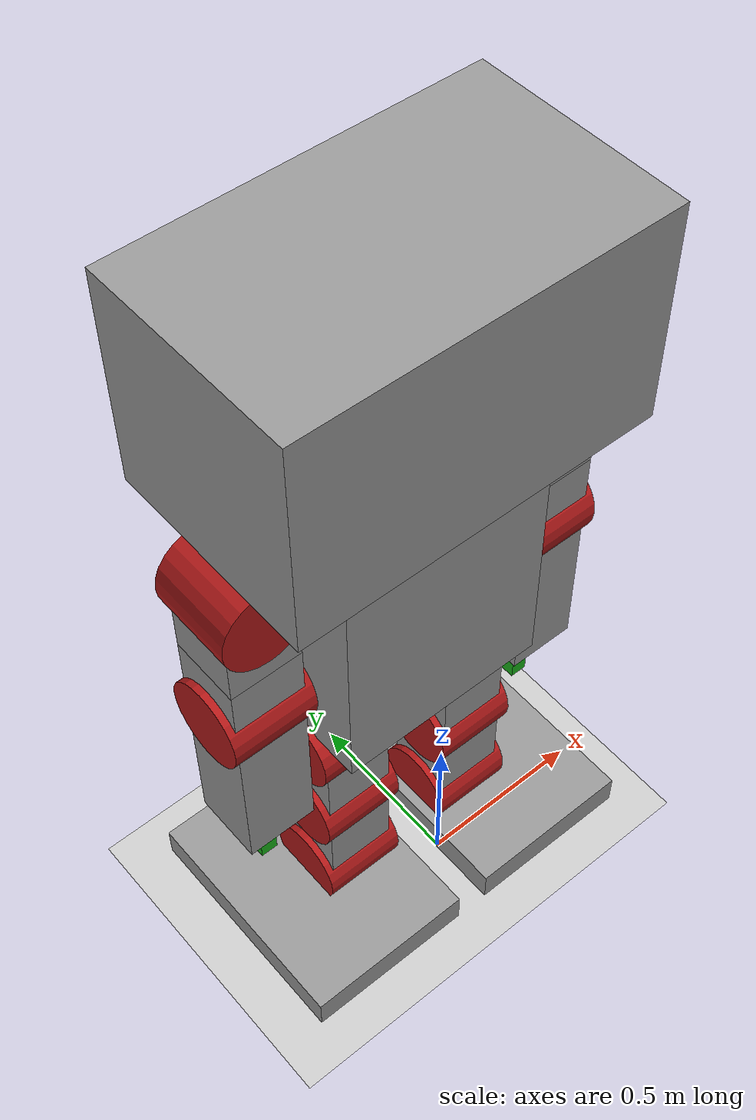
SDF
<sdf version="1.5">
 <world name="default">
  <light name="sun" type="directional">
   <pose>0 0 10 0.6 -0 0</pose>
   <diffuse>0.8 0.8 0.8 1</diffuse>
   <specular>0.2 0.2 0.2 1</specular>
   <attenuation>
    <range>1000</range>
    <constant>0.9</constant>
    <linear>0.01</linear>
    <quadratic>0.001</quadratic>
   </attenuation>
   <direction>-0.5 0.1 -0.9</direction>
  </light>
  <model name="ground_plane">
   <static>1</static>
   <link name="link">
    <collision name="collision">
     <geometry><plane><normal>0 0 1</normal><size>100 100</size></plane></geometry>
     <surface><friction><ode><mu>100</mu><mu2>50</mu2></ode></friction></surface>
    </collision>
    <visual name="visual">
     <cast_shadows>0</cast_shadows>
     <geometry><plane><normal>0 0 1</normal><size>100 100</size></plane></geometry>
     <material>
      <script><uri>file://media/materials/scripts/gazebo.material</uri><name>Gazebo/Grey</name></script>
     </material>
    </visual>
   </link>
  </model>
  <physics name="default_physics" default="0" type="ode">
   <max_step_size>0.001</max_step_size>
   <real_time_factor>1</real_time_factor>
   <real_time_update_rate>1000</real_time_update_rate>
   <gravity>0 0 -9.8</gravity>
   <magnetic_field>6e-06 2.3e-05 -4.2e-05</magnetic_field>
   <roki>
    <contact_info>
     <compensation>100</compensation>
     <relaxation>0.001</relaxation>
     <static_friction>3.0</static_friction>
     <friction>3.0</friction>
    </contact_info>
    <solver_type>Vert</solver_type>
    <debug_print>false</debug_print>
   </roki>
  </physics>
  <scene><ambient>0.4 0.4 0.4 1</ambient><background>0.7 0.7 0.7 1</background><shadows>1</shadows></scene>
  <audio><device>default</device></audio>
  <spherical_coordinates>
   <surface_model>EARTH_WGS84</surface_model>
   <latitude_deg>0</latitude_deg>
   <longitude_deg>0</longitude_deg>
   <elevation>0</elevation>
   <heading_deg>0</heading_deg>
  </spherical_coordinates>
  <model name="robo02">
   <plugin name="osc_pid_controller" filename="libosc_pid_controller_plugin.so">
    <osc_port>7000</osc_port>
    <joint name="hip_r_pitch" p="160" i="160" d="140" initial_value="0"/>
    <joint name="knee_r_pitch" p="160" i="160" d="140" initial_value="0"/>
    <joint name="heel_r_pitch" p="160" i="160" d="140" initial_value="0"/>
    <joint name="hip_l_pitch" p="160" i="160" d="140" initial_value="0"/>
    <joint name="knee_l_pitch" p="160" i="160" d="140" initial_value="0"/>
    <joint name="heel_l_pitch" p="160" i="160" d="140" initial_value="0"/>
    <joint name="shoulder_r_pitch" p="20" i="10" d="10" initial_value="0"/>
    <joint name="shoulder_r_roll" p="20" i="10" d="10" initial_value="0"/>
    <joint name="shoulder_r_yaw" p="20" i="10" d="10" initial_value="0"/>
    <joint name="elbow_r_pitch" p="20" i="10" d="10" initial_value="0"/>
    <joint name="shoulder_l_pitch" p="20" i="10" d="10" initial_value="0"/>
    <joint name="shoulder_l_roll" p="20" i="10" d="10" initial_value="0"/>
    <joint name="shoulder_l_yaw" p="20" i="10" d="10" initial_value="0"/>
    <joint name="elbow_l_pitch" p="20" i="10" d="10" initial_value="0"/>
    <capture_file>/home/test/capture.csv</capture_file>
   </plugin>
   <link name="link_0">
    <pose>-0.266944 -0.109722 1.83351 0 -0 0</pose>
    <inertial>
     <mass>1</mass>
     <inertia><ixx>1</ixx><ixy>0</ixy><ixz>0</ixz><iyy>1</iyy><iyz>0</iyz><izz>1</izz></inertia>
    </inertial>
    <visual name="visual">
     <geometry><box><size>0.6 0.4 0.8</size></box></geometry>
     <material>
      <lighting>1</lighting>
      <script><uri>file://media/materials/scripts/gazebo.material</uri><name>Gazebo/Grey</name></script>
      <shader type="pixel"><normal_map>__default__</normal_map></shader>
      <ambient>0.3 0.3 0.3 1</ambient>
      <diffuse>0.7 0.7 0.7 1</diffuse>
      <specular>0.01 0.01 0.01 1</specular>
      <emissive>0 0 0 1</emissive>
     </material>
    </visual>
    <collision name="collision">
     <geometry><box><size>0.6 0.4 0.8</size></box></geometry>
     <surface>
      <friction><ode><mu>1</mu><mu2>1</mu2><fdir1>0 0 0</fdir1><slip1>0</slip1><slip2>0</slip2></ode></friction>
      <bounce><restitution_coefficient>0</restitution_coefficient><threshold>1e+06</threshold></bounce>
      <contact>
       <collide_without_contact>0</collide_without_contact>
       <collide_without_contact_bitmask>1</collide_without_contact_bitmask>
       <collide_bitmask>1</collide_bitmask>
       <ode>
        <soft_cfm>0</soft_cfm>
        <soft_erp>0.2</soft_erp>
        <kp>1e+13</kp>
        <kd>1</kd>
        <max_vel>0.01</max_vel>
        <min_depth>0</min_depth>
       </ode>
       <bullet>
        <split_impulse>1</split_impulse>
        <split_impulse_penetration_threshold>-0.01</split_impulse_penetration_threshold>
        <soft_cfm>0</soft_cfm>
        <soft_erp>0.2</soft_erp>
        <kp>1e+13</kp>
        <kd>1</kd>
       </bullet>
      </contact>
     </surface>
    </collision>
   </link>
   <link name="link_1">
    <pose>-0.266944 -0.109722 2.53351 0 -0 0</pose>
    <inertial>
     <mass>0.1</mass>
     <inertia><ixx>1</ixx><ixy>0</ixy><ixz>0</ixz><iyy>1</iyy><iyz>0</iyz><izz>1</izz></inertia>
    </inertial>
    <visual name="visual">
     <geometry><box><size>1 0.6 0.6</size></box></geometry>
     <material>
      <lighting>1</lighting>
      <script><uri>file://media/materials/scripts/gazebo.material</uri><name>Gazebo/Grey</name></script>
      <shader type="pixel"><normal_map>__default__</normal_map></shader>
      <ambient>0.3 0.3 0.3 1</ambient>
      <diffuse>0.7 0.7 0.7 1</diffuse>
      <specular>0.01 0.01 0.01 1</specular>
      <emissive>0 0 0 1</emissive>
     </material>
    </visual>
    <collision name="collision">
     <geometry><box><size>1 0.6 0.6</size></box></geometry>
     <surface>
      <friction><ode><mu>1</mu><mu2>1</mu2><fdir1>0 0 0</fdir1><slip1>0</slip1><slip2>0</slip2></ode></friction>
      <bounce><restitution_coefficient>0</restitution_coefficient><threshold>1e+06</threshold></bounce>
      <contact>
       <collide_without_contact>0</collide_without_contact>
       <collide_without_contact_bitmask>1</collide_without_contact_bitmask>
       <collide_bitmask>1</collide_bitmask>
       <ode>
        <soft_cfm>0</soft_cfm>
        <soft_erp>0.2</soft_erp>
        <kp>1e+13</kp>
        <kd>1</kd>
        <max_vel>0.01</max_vel>
        <min_depth>0</min_depth>
       </ode>
       <bullet>
        <split_impulse>1</split_impulse>
        <split_impulse_penetration_threshold>-0.01</split_impulse_penetration_threshold>
        <soft_cfm>0</soft_cfm>
        <soft_erp>0.2</soft_erp>
        <kp>1e+13</kp>
        <kd>1</kd>
       </bullet>
      </contact>
     </surface>
    </collision>
   </link>
   <link name="link_11">
    <pose>0.183056 -0.109722 1.98351 0 -0 0</pose>
    <inertial>
     <mass>2</mass>
     <inertia><ixx>1</ixx><ixy>0</ixy><ixz>0</ixz><iyy>1</iyy><iyz>0</iyz><izz>1</izz></inertia>
    </inertial>
    <visual name="visual">
     <geometry><box><size>0.2 0.2 0.2</size></box></geometry>
     <material>
      <lighting>1</lighting>
      <script><uri>file://media/materials/scripts/gazebo.material</uri><name>Gazebo/Grey</name></script>
      <shader type="pixel"><normal_map>__default__</normal_map></shader>
      <ambient>0.3 0.3 0.3 1</ambient>
      <diffuse>0.7 0.7 0.7 1</diffuse>
      <specular>0.01 0.01 0.01 1</specular>
      <emissive>0 0 0 1</emissive>
     </material>
    </visual>
    <collision name="collision">
     <geometry><box><size>0.2 0.2 0.2</size></box></geometry>
     <surface>
      <friction><ode><mu>1</mu><mu2>1</mu2><fdir1>0 0 0</fdir1><slip1>0</slip1><slip2>0</slip2></ode></friction>
      <bounce><restitution_coefficient>0</restitution_coefficient><threshold>1e+06</threshold></bounce>
      <contact>
       <collide_without_contact>0</collide_without_contact>
       <collide_without_contact_bitmask>1</collide_without_contact_bitmask>
       <collide_bitmask>1</collide_bitmask>
       <ode>
        <soft_cfm>0</soft_cfm>
        <soft_erp>0.2</soft_erp>
        <kp>1e+13</kp>
        <kd>1</kd>
        <max_vel>0.01</max_vel>
        <min_depth>0</min_depth>
       </ode>
       <bullet>
        <split_impulse>1</split_impulse>
        <split_impulse_penetration_threshold>-0.01</split_impulse_penetration_threshold>
        <soft_cfm>0</soft_cfm>
        <soft_erp>0.2</soft_erp>
        <kp>1e+13</kp>
        <kd>1</kd>
       </bullet>
      </contact>
     </surface>
    </collision>
   </link>
   <link name="link_12">
    <pose>0.183056 -0.109722 1.78351 0 -0 0</pose>
    <inertial>
     <mass>0.2</mass>
     <inertia><ixx>1</ixx><ixy>0</ixy><ixz>0</ixz><iyy>1</iyy><iyz>0</iyz><izz>1</izz></inertia>
    </inertial>
    <visual name="visual">
     <geometry><box><size>0.2 0.2 0.2</size></box></geometry>
     <material>
      <lighting>1</lighting>
      <script><uri>file://media/materials/scripts/gazebo.material</uri><name>Gazebo/Grey</name></script>
      <shader type="pixel"><normal_map>__default__</normal_map></shader>
      <ambient>0.3 0.3 0.3 1</ambient>
      <diffuse>0.7 0.7 0.7 1</diffuse>
      <specular>0.01 0.01 0.01 1</specular>
      <emissive>0 0 0 1</emissive>
     </material>
    </visual>
    <collision name="collision">
     <geometry><box><size>0.2 0.2 0.2</size></box></geometry>
     <surface>
      <friction><ode><mu>1</mu><mu2>1</mu2><fdir1>0 0 0</fdir1><slip1>0</slip1><slip2>0</slip2></ode></friction>
      <bounce><restitution_coefficient>0</restitution_coefficient><threshold>1e+06</threshold></bounce>
      <contact>
       <collide_without_contact>0</collide_without_contact>
       <collide_without_contact_bitmask>1</collide_without_contact_bitmask>
       <collide_bitmask>1</collide_bitmask>
       <ode>
        <soft_cfm>0</soft_cfm>
        <soft_erp>0.2</soft_erp>
        <kp>1e+13</kp>
        <kd>1</kd>
        <max_vel>0.01</max_vel>
        <min_depth>0</min_depth>
       </ode>
       <bullet>
        <split_impulse>1</split_impulse>
        <split_impulse_penetration_threshold>-0.01</split_impulse_penetration_threshold>
        <soft_cfm>0</soft_cfm>
        <soft_erp>0.2</soft_erp>
        <kp>1e+13</kp>
        <kd>1</kd>
       </bullet>
      </contact>
     </surface>
    </collision>
   </link>
   <link name="link_13">
    <pose>0.183056 -0.109722 1.68351 3.14159 1.57079 3.14159</pose>
    <inertial>
     <mass>0.1</mass>
     <inertia><ixx>1</ixx><ixy>0</ixy><ixz>0</ixz><iyy>1</iyy><iyz>0</iyz><izz>1</izz></inertia>
    </inertial>
    <visual name="visual">
     <geometry><cylinder><radius>0.12</radius><length>0.24</length></cylinder></geometry>
     <material>
      <lighting>1</lighting>
      <script><uri>file://media/materials/scripts/gazebo.material</uri><name>Gazebo/Grey</name></script>
      <shader type="pixel"><normal_map>__default__</normal_map></shader>
      <ambient>0.3 0.3 0.3 1</ambient>
      <diffuse>0.7 0.1 0.1 1</diffuse>
      <specular>0.01 0.01 0.01 1</specular>
      <emissive>0 0 0 1</emissive>
     </material>
    </visual>
    <collision name="collision">
     <geometry><cylinder><radius>0.12</radius><length>0.24</length></cylinder></geometry>
     <surface>
      <friction><ode><mu>1</mu><mu2>1</mu2><fdir1>0 0 0</fdir1><slip1>0</slip1><slip2>0</slip2></ode></friction>
      <bounce><restitution_coefficient>0</restitution_coefficient><threshold>1e+06</threshold></bounce>
      <contact>
       <collide_without_contact>0</collide_without_contact>
       <collide_without_contact_bitmask>1</collide_without_contact_bitmask>
       <collide_bitmask>1</collide_bitmask>
       <ode>
        <soft_cfm>0</soft_cfm>
        <soft_erp>0.2</soft_erp>
        <kp>1e+13</kp>
        <kd>1</kd>
        <max_vel>0.01</max_vel>
        <min_depth>0</min_depth>
       </ode>
       <bullet>
        <split_impulse>1</split_impulse>
        <split_impulse_penetration_threshold>-0.01</split_impulse_penetration_threshold>
        <soft_cfm>0</soft_cfm>
        <soft_erp>0.2</soft_erp>
        <kp>1e+13</kp>
        <kd>1</kd>
       </bullet>
      </contact>
     </surface>
    </collision>
   </link>
   <link name="link_14">
    <pose>0.183056 -0.109722 1.43351 0 -0 0</pose>
    <inertial>
     <mass>0.2</mass>
     <inertia><ixx>1</ixx><ixy>0</ixy><ixz>0</ixz><iyy>1</iyy><iyz>0</iyz><izz>1</izz></inertia>
    </inertial>
    <visual name="visual">
     <geometry><box><size>0.2 0.2 0.5</size></box></geometry>
     <material>
      <lighting>1</lighting>
      <script><uri>file://media/materials/scripts/gazebo.material</uri><name>Gazebo/Grey</name></script>
      <shader type="pixel"><normal_map>__default__</normal_map></shader>
      <ambient>0.3 0.3 0.3 1</ambient>
      <diffuse>0.7 0.7 0.7 1</diffuse>
      <specular>0.01 0.01 0.01 1</specular>
      <emissive>0 0 0 1</emissive>
     </material>
    </visual>
    <collision name="collision">
     <geometry><box><size>0.2 0.2 0.5</size></box></geometry>
     <surface>
      <friction><ode><mu>1</mu><mu2>1</mu2><fdir1>0 0 0</fdir1><slip1>0</slip1><slip2>0</slip2></ode></friction>
      <bounce><restitution_coefficient>0</restitution_coefficient><threshold>1e+06</threshold></bounce>
      <contact>
       <collide_without_contact>0</collide_without_contact>
       <collide_without_contact_bitmask>1</collide_without_contact_bitmask>
       <collide_bitmask>1</collide_bitmask>
       <ode>
        <soft_cfm>0</soft_cfm>
        <soft_erp>0.2</soft_erp>
        <kp>1e+13</kp>
        <kd>1</kd>
        <max_vel>0.01</max_vel>
        <min_depth>0</min_depth>
       </ode>
       <bullet>
        <split_impulse>1</split_impulse>
        <split_impulse_penetration_threshold>-0.01</split_impulse_penetration_threshold>
        <soft_cfm>0</soft_cfm>
        <soft_erp>0.2</soft_erp>
        <kp>1e+13</kp>
        <kd>1</kd>
       </bullet>
      </contact>
     </surface>
    </collision>
   </link>
   <link name="link_15">
    <pose>-0.466944 -0.109722 1.33351 3.14159 1.57079 3.14159</pose>
    <inertial>
     <mass>0.1</mass>
     <inertia><ixx>1</ixx><ixy>0</ixy><ixz>0</ixz><iyy>1</iyy><iyz>0</iyz><izz>1</izz></inertia>
    </inertial>
    <visual name="visual">
     <geometry><cylinder><radius>0.12</radius><length>0.24</length></cylinder></geometry>
     <material>
      <lighting>1</lighting>
      <script><uri>file://media/materials/scripts/gazebo.material</uri><name>Gazebo/Grey</name></script>
      <shader type="pixel"><normal_map>__default__</normal_map></shader>
      <ambient>0.3 0.3 0.3 1</ambient>
      <diffuse>0.7 0.1 0.1 1</diffuse>
      <specular>0.01 0.01 0.01 1</specular>
      <emissive>0 0 0 1</emissive>
     </material>
    </visual>
    <collision name="collision">
     <geometry><cylinder><radius>0.12</radius><length>0.24</length></cylinder></geometry>
     <surface>
      <friction><ode><mu>1</mu><mu2>1</mu2><fdir1>0 0 0</fdir1><slip1>0</slip1><slip2>0</slip2></ode></friction>
      <bounce><restitution_coefficient>0</restitution_coefficient><threshold>1e+06</threshold></bounce>
      <contact>
       <collide_without_contact>0</collide_without_contact>
       <collide_without_contact_bitmask>1</collide_without_contact_bitmask>
       <collide_bitmask>1</collide_bitmask>
       <ode>
        <soft_cfm>0</soft_cfm>
        <soft_erp>0.2</soft_erp>
        <kp>1e+13</kp>
        <kd>1</kd>
        <max_vel>0.01</max_vel>
        <min_depth>0</min_depth>
       </ode>
       <bullet>
        <split_impulse>1</split_impulse>
        <split_impulse_penetration_threshold>-0.01</split_impulse_penetration_threshold>
        <soft_cfm>0</soft_cfm>
        <soft_erp>0.2</soft_erp>
        <kp>1e+13</kp>
        <kd>1</kd>
       </bullet>
      </contact>
     </surface>
    </collision>
   </link>
   <link name="link_16">
    <pose>-0.466944 -0.109722 1.18351 0 -0 0</pose>
    <inertial>
     <mass>0.2</mass>
     <inertia><ixx>1</ixx><ixy>0</ixy><ixz>0</ixz><iyy>1</iyy><iyz>0</iyz><izz>1</izz></inertia>
    </inertial>
    <visual name="visual">
     <geometry><box><size>0.2 0.2 0.3</size></box></geometry>
     <material>
      <lighting>1</lighting>
      <script><uri>file://media/materials/scripts/gazebo.material</uri><name>Gazebo/Grey</name></script>
      <shader type="pixel"><normal_map>__default__</normal_map></shader>
      <ambient>0.3 0.3 0.3 1</ambient>
      <diffuse>0.7 0.7 0.7 1</diffuse>
      <specular>0.01 0.01 0.01 1</specular>
      <emissive>0 0 0 1</emissive>
     </material>
    </visual>
    <collision name="collision">
     <geometry><box><size>0.2 0.2 0.3</size></box></geometry>
     <surface>
      <friction><ode><mu>1</mu><mu2>1</mu2><fdir1>0 0 0</fdir1><slip1>0</slip1><slip2>0</slip2></ode></friction>
      <bounce><restitution_coefficient>0</restitution_coefficient><threshold>1e+06</threshold></bounce>
      <contact>
       <collide_without_contact>0</collide_without_contact>
       <collide_without_contact_bitmask>1</collide_without_contact_bitmask>
       <collide_bitmask>1</collide_bitmask>
       <ode>
        <soft_cfm>0</soft_cfm>
        <soft_erp>0.2</soft_erp>
        <kp>1e+13</kp>
        <kd>1</kd>
        <max_vel>0.01</max_vel>
        <min_depth>0</min_depth>
       </ode>
       <bullet>
        <split_impulse>1</split_impulse>
        <split_impulse_penetration_threshold>-0.01</split_impulse_penetration_threshold>
        <soft_cfm>0</soft_cfm>
        <soft_erp>0.2</soft_erp>
        <kp>1e+13</kp>
        <kd>1</kd>
       </bullet>
      </contact>
     </surface>
    </collision>
   </link>
   <link name="link_17">
    <pose>-0.466944 -0.109722 1.03351 3.14159 1.57079 3.14159</pose>
    <inertial>
     <mass>0.1</mass>
     <inertia><ixx>1</ixx><ixy>0</ixy><ixz>0</ixz><iyy>1</iyy><iyz>0</iyz><izz>1</izz></inertia>
    </inertial>
    <visual name="visual">
     <geometry><cylinder><radius>0.12</radius><length>0.24</length></cylinder></geometry>
     <material>
      <lighting>1</lighting>
      <script><uri>file://media/materials/scripts/gazebo.material</uri><name>Gazebo/Grey</name></script>
      <shader type="pixel"><normal_map>__default__</normal_map></shader>
      <ambient>0.3 0.3 0.3 1</ambient>
      <diffuse>0.7 0.1 0.1 1</diffuse>
      <specular>0.01 0.01 0.01 1</specular>
      <emissive>0 0 0 1</emissive>
     </material>
    </visual>
    <collision name="collision">
     <geometry><cylinder><radius>0.12</radius><length>0.24</length></cylinder></geometry>
     <surface>
      <friction><ode><mu>1</mu><mu2>1</mu2><fdir1>0 0 0</fdir1><slip1>0</slip1><slip2>0</slip2></ode></friction>
      <bounce><restitution_coefficient>0</restitution_coefficient><threshold>1e+06</threshold></bounce>
      <contact>
       <collide_without_contact>0</collide_without_contact>
       <collide_without_contact_bitmask>1</collide_without_contact_bitmask>
       <collide_bitmask>1</collide_bitmask>
       <ode>
        <soft_cfm>0</soft_cfm>
        <soft_erp>0.2</soft_erp>
        <kp>1e+13</kp>
        <kd>1</kd>
        <max_vel>0.01</max_vel>
        <min_depth>0</min_depth>
       </ode>
       <bullet>
        <split_impulse>1</split_impulse>
        <split_impulse_penetration_threshold>-0.01</split_impulse_penetration_threshold>
        <soft_cfm>0</soft_cfm>
        <soft_erp>0.2</soft_erp>
        <kp>1e+13</kp>
        <kd>1</kd>
       </bullet>
      </contact>
     </surface>
    </collision>
   </link>
   <link name="link_18">
    <pose>-0.466944 -0.109722 0.883512 0 -0 0</pose>
    <inertial>
     <mass>0.2</mass>
     <inertia><ixx>1</ixx><ixy>0</ixy><ixz>0</ixz><iyy>1</iyy><iyz>0</iyz><izz>1</izz></inertia>
    </inertial>
    <visual name="visual">
     <geometry><box><size>0.2 0.2 0.3</size></box></geometry>
     <material>
      <lighting>1</lighting>
      <script><uri>file://media/materials/scripts/gazebo.material</uri><name>Gazebo/Grey</name></script>
      <shader type="pixel"><normal_map>__default__</normal_map></shader>
      <ambient>0.3 0.3 0.3 1</ambient>
      <diffuse>0.7 0.7 0.7 1</diffuse>
      <specular>0.01 0.01 0.01 1</specular>
      <emissive>0 0 0 1</emissive>
     </material>
    </visual>
    <collision name="collision">
     <geometry><box><size>0.2 0.2 0.3</size></box></geometry>
     <surface>
      <friction><ode><mu>1</mu><mu2>1</mu2><fdir1>0 0 0</fdir1><slip1>0</slip1><slip2>0</slip2></ode></friction>
      <bounce><restitution_coefficient>0</restitution_coefficient><threshold>1e+06</threshold></bounce>
      <contact>
       <collide_without_contact>0</collide_without_contact>
       <collide_without_contact_bitmask>1</collide_without_contact_bitmask>
       <collide_bitmask>1</collide_bitmask>
       <ode>
        <soft_cfm>0</soft_cfm>
        <soft_erp>0.2</soft_erp>
        <kp>1e+13</kp>
        <kd>1</kd>
        <max_vel>0.01</max_vel>
        <min_depth>0</min_depth>
       </ode>
       <bullet>
        <split_impulse>1</split_impulse>
        <split_impulse_penetration_threshold>-0.01</split_impulse_penetration_threshold>
        <soft_cfm>0</soft_cfm>
        <soft_erp>0.2</soft_erp>
        <kp>1e+13</kp>
        <kd>1</kd>
       </bullet>
      </contact>
     </surface>
    </collision>
   </link>
   <link name="link_20">
    <pose>-0.466944 -0.109722 0.733512 3.14159 1.57079 3.14159</pose>
    <inertial>
     <mass>0.1</mass>
     <inertia><ixx>1</ixx><ixy>0</ixy><ixz>0</ixz><iyy>1</iyy><iyz>0</iyz><izz>1</izz></inertia>
    </inertial>
    <visual name="visual">
     <geometry><cylinder><radius>0.12</radius><length>0.24</length></cylinder></geometry>
     <material>
      <lighting>1</lighting>
      <script><uri>file://media/materials/scripts/gazebo.material</uri><name>Gazebo/Grey</name></script>
      <shader type="pixel"><normal_map>__default__</normal_map></shader>
      <ambient>0.3 0.3 0.3 1</ambient>
      <diffuse>0.7 0.1 0.1 1</diffuse>
      <specular>0.01 0.01 0.01 1</specular>
      <emissive>0 0 0 1</emissive>
     </material>
    </visual>
    <collision name="collision">
     <geometry><cylinder><radius>0.12</radius><length>0.24</length></cylinder></geometry>
     <surface>
      <friction><ode><mu>1</mu><mu2>1</mu2><fdir1>0 0 0</fdir1><slip1>0</slip1><slip2>0</slip2></ode></friction>
      <bounce><restitution_coefficient>0</restitution_coefficient><threshold>1e+06</threshold></bounce>
      <contact>
       <collide_without_contact>0</collide_without_contact>
       <collide_without_contact_bitmask>1</collide_without_contact_bitmask>
       <collide_bitmask>1</collide_bitmask>
       <ode>
        <soft_cfm>0</soft_cfm>
        <soft_erp>0.2</soft_erp>
        <kp>1e+13</kp>
        <kd>1</kd>
        <max_vel>0.01</max_vel>
        <min_depth>0</min_depth>
       </ode>
       <bullet>
        <split_impulse>1</split_impulse>
        <split_impulse_penetration_threshold>-0.01</split_impulse_penetration_threshold>
        <soft_cfm>0</soft_cfm>
        <soft_erp>0.2</soft_erp>
        <kp>1e+13</kp>
        <kd>1</kd>
       </bullet>
      </contact>
     </surface>
    </collision>
   </link>
   <link name="link_22">
    <pose>-0.566944 -0.109722 0.633512 0 -0 0</pose>
    <inertial>
     <mass>2</mass>
     <inertia><ixx>1</ixx><ixy>0</ixy><ixz>0</ixz><iyy>1</iyy><iyz>0</iyz><izz>1</izz></inertia>
    </inertial>
    <visual name="visual">
     <geometry><box><size>0.5 0.7 0.1</size></box></geometry>
     <material>
      <lighting>1</lighting>
      <script><uri>file://media/materials/scripts/gazebo.material</uri><name>Gazebo/Grey</name></script>
      <shader type="pixel"><normal_map>__default__</normal_map></shader>
      <ambient>0.3 0.3 0.3 1</ambient>
      <diffuse>0.7 0.7 0.7 1</diffuse>
      <specular>0.01 0.01 0.01 1</specular>
      <emissive>0 0 0 1</emissive>
     </material>
    </visual>
    <collision name="collision">
     <geometry><box><size>0.5 0.7 0.1</size></box></geometry>
     <surface>
      <friction><ode><mu>1</mu><mu2>1</mu2><fdir1>0 0 0</fdir1><slip1>0</slip1><slip2>0</slip2></ode></friction>
      <bounce><restitution_coefficient>0</restitution_coefficient><threshold>1e+06</threshold></bounce>
      <contact>
       <collide_without_contact>0</collide_without_contact>
       <collide_without_contact_bitmask>1</collide_without_contact_bitmask>
       <collide_bitmask>1</collide_bitmask>
       <ode>
        <soft_cfm>0</soft_cfm>
        <soft_erp>0.2</soft_erp>
        <kp>1e+13</kp>
        <kd>1</kd>
        <max_vel>0.01</max_vel>
        <min_depth>0</min_depth>
       </ode>
       <bullet>
        <split_impulse>1</split_impulse>
        <split_impulse_penetration_threshold>-0.01</split_impulse_penetration_threshold>
        <soft_cfm>0</soft_cfm>
        <soft_erp>0.2</soft_erp>
        <kp>1e+13</kp>
        <kd>1</kd>
       </bullet>
      </contact>
     </surface>
    </collision>
   </link>
   <link name="link_23">
    <pose>-0.066944 -0.109722 1.33351 3.14159 1.57079 3.14159</pose>
    <inertial>
     <mass>0.1</mass>
     <inertia><ixx>1</ixx><ixy>0</ixy><ixz>0</ixz><iyy>1</iyy><iyz>0</iyz><izz>1</izz></inertia>
    </inertial>
    <visual name="visual">
     <geometry><cylinder><radius>0.12</radius><length>0.24</length></cylinder></geometry>
     <material>
      <lighting>1</lighting>
      <script><uri>file://media/materials/scripts/gazebo.material</uri><name>Gazebo/Grey</name></script>
      <shader type="pixel"><normal_map>__default__</normal_map></shader>
      <ambient>0.3 0.3 0.3 1</ambient>
      <diffuse>0.7 0.1 0.1 1</diffuse>
      <specular>0.01 0.01 0.01 1</specular>
      <emissive>0 0 0 1</emissive>
     </material>
    </visual>
    <collision name="collision">
     <geometry><cylinder><radius>0.12</radius><length>0.24</length></cylinder></geometry>
     <surface>
      <friction><ode><mu>1</mu><mu2>1</mu2><fdir1>0 0 0</fdir1><slip1>0</slip1><slip2>0</slip2></ode></friction>
      <bounce><restitution_coefficient>0</restitution_coefficient><threshold>1e+06</threshold></bounce>
      <contact>
       <collide_without_contact>0</collide_without_contact>
       <collide_without_contact_bitmask>1</collide_without_contact_bitmask>
       <collide_bitmask>1</collide_bitmask>
       <ode>
        <soft_cfm>0</soft_cfm>
        <soft_erp>0.2</soft_erp>
        <kp>1e+13</kp>
        <kd>1</kd>
        <max_vel>0.01</max_vel>
        <min_depth>0</min_depth>
       </ode>
       <bullet>
        <split_impulse>1</split_impulse>
        <split_impulse_penetration_threshold>-0.01</split_impulse_penetration_threshold>
        <soft_cfm>0</soft_cfm>
        <soft_erp>0.2</soft_erp>
        <kp>1e+13</kp>
        <kd>1</kd>
       </bullet>
      </contact>
     </surface>
    </collision>
   </link>
   <link name="link_24">
    <pose>-0.066944 -0.109722 1.18351 0 -0 0</pose>
    <inertial>
     <mass>0.2</mass>
     <inertia><ixx>1</ixx><ixy>0</ixy><ixz>0</ixz><iyy>1</iyy><iyz>0</iyz><izz>1</izz></inertia>
    </inertial>
    <visual name="visual">
     <geometry><box><size>0.2 0.2 0.3</size></box></geometry>
     <material>
      <lighting>1</lighting>
      <script><uri>file://media/materials/scripts/gazebo.material</uri><name>Gazebo/Grey</name></script>
      <shader type="pixel"><normal_map>__default__</normal_map></shader>
      <ambient>0.3 0.3 0.3 1</ambient>
      <diffuse>0.7 0.7 0.7 1</diffuse>
      <specular>0.01 0.01 0.01 1</specular>
      <emissive>0 0 0 1</emissive>
     </material>
    </visual>
    <collision name="collision">
     <geometry><box><size>0.2 0.2 0.3</size></box></geometry>
     <surface>
      <friction><ode><mu>1</mu><mu2>1</mu2><fdir1>0 0 0</fdir1><slip1>0</slip1><slip2>0</slip2></ode></friction>
      <bounce><restitution_coefficient>0</restitution_coefficient><threshold>1e+06</threshold></bounce>
      <contact>
       <collide_without_contact>0</collide_without_contact>
       <collide_without_contact_bitmask>1</collide_without_contact_bitmask>
       <collide_bitmask>1</collide_bitmask>
       <ode>
        <soft_cfm>0</soft_cfm>
        <soft_erp>0.2</soft_erp>
        <kp>1e+13</kp>
        <kd>1</kd>
        <max_vel>0.01</max_vel>
        <min_depth>0</min_depth>
       </ode>
       <bullet>
        <split_impulse>1</split_impulse>
        <split_impulse_penetration_threshold>-0.01</split_impulse_penetration_threshold>
        <soft_cfm>0</soft_cfm>
        <soft_erp>0.2</soft_erp>
        <kp>1e+13</kp>
        <kd>1</kd>
       </bullet>
      </contact>
     </surface>
    </collision>
   </link>
   <link name="link_25">
    <pose>-0.066944 -0.109722 1.03351 3.14159 1.57079 3.14159</pose>
    <inertial>
     <mass>0.1</mass>
     <inertia><ixx>1</ixx><ixy>0</ixy><ixz>0</ixz><iyy>1</iyy><iyz>0</iyz><izz>1</izz></inertia>
    </inertial>
    <visual name="visual">
     <geometry><cylinder><radius>0.12</radius><length>0.24</length></cylinder></geometry>
     <material>
      <lighting>1</lighting>
      <script><uri>file://media/materials/scripts/gazebo.material</uri><name>Gazebo/Grey</name></script>
      <shader type="pixel"><normal_map>__default__</normal_map></shader>
      <ambient>0.3 0.3 0.3 1</ambient>
      <diffuse>0.7 0.1 0.1 1</diffuse>
      <specular>0.01 0.01 0.01 1</specular>
      <emissive>0 0 0 1</emissive>
     </material>
    </visual>
    <collision name="collision">
     <geometry><cylinder><radius>0.12</radius><length>0.24</length></cylinder></geometry>
     <surface>
      <friction><ode><mu>1</mu><mu2>1</mu2><fdir1>0 0 0</fdir1><slip1>0</slip1><slip2>0</slip2></ode></friction>
      <bounce><restitution_coefficient>0</restitution_coefficient><threshold>1e+06</threshold></bounce>
      <contact>
       <collide_without_contact>0</collide_without_contact>
       <collide_without_contact_bitmask>1</collide_without_contact_bitmask>
       <collide_bitmask>1</collide_bitmask>
       <ode>
        <soft_cfm>0</soft_cfm>
        <soft_erp>0.2</soft_erp>
        <kp>1e+13</kp>
        <kd>1</kd>
        <max_vel>0.01</max_vel>
        <min_depth>0</min_depth>
       </ode>
       <bullet>
        <split_impulse>1</split_impulse>
        <split_impulse_penetration_threshold>-0.01</split_impulse_penetration_threshold>
        <soft_cfm>0</soft_cfm>
        <soft_erp>0.2</soft_erp>
        <kp>1e+13</kp>
        <kd>1</kd>
       </bullet>
      </contact>
     </surface>
    </collision>
   </link>
   <link name="link_26">
    <pose>-0.066944 -0.109722 0.883512 0 -0 0</pose>
    <inertial>
     <mass>0.2</mass>
     <inertia><ixx>1</ixx><ixy>0</ixy><ixz>0</ixz><iyy>1</iyy><iyz>0</iyz><izz>1</izz></inertia>
    </inertial>
    <visual name="visual">
     <geometry><box><size>0.2 0.2 0.3</size></box></geometry>
     <material>
      <lighting>1</lighting>
      <script><uri>file://media/materials/scripts/gazebo.material</uri><name>Gazebo/Grey</name></script>
      <shader type="pixel"><normal_map>__default__</normal_map></shader>
      <ambient>0.3 0.3 0.3 1</ambient>
      <diffuse>0.7 0.7 0.7 1</diffuse>
      <specular>0.01 0.01 0.01 1</specular>
      <emissive>0 0 0 1</emissive>
     </material>
    </visual>
    <collision name="collision">
     <geometry><box><size>0.2 0.2 0.3</size></box></geometry>
     <surface>
      <friction><ode><mu>1</mu><mu2>1</mu2><fdir1>0 0 0</fdir1><slip1>0</slip1><slip2>0</slip2></ode></friction>
      <bounce><restitution_coefficient>0</restitution_coefficient><threshold>1e+06</threshold></bounce>
      <contact>
       <collide_without_contact>0</collide_without_contact>
       <collide_without_contact_bitmask>1</collide_without_contact_bitmask>
       <collide_bitmask>1</collide_bitmask>
       <ode>
        <soft_cfm>0</soft_cfm>
        <soft_erp>0.2</soft_erp>
        <kp>1e+13</kp>
        <kd>1</kd>
        <max_vel>0.01</max_vel>
        <min_depth>0</min_depth>
       </ode>
       <bullet>
        <split_impulse>1</split_impulse>
        <split_impulse_penetration_threshold>-0.01</split_impulse_penetration_threshold>
        <soft_cfm>0</soft_cfm>
        <soft_erp>0.2</soft_erp>
        <kp>1e+13</kp>
        <kd>1</kd>
       </bullet>
      </contact>
     </surface>
    </collision>
   </link>
   <link name="link_28">
    <pose>-0.066944 -0.109722 0.733512 0 1.5706 0</pose>
    <inertial>
     <mass>0.1</mass>
     <inertia><ixx>1</ixx><ixy>0</ixy><ixz>0</ixz><iyy>1</iyy><iyz>0</iyz><izz>1</izz></inertia>
    </inertial>
    <visual name="visual">
     <geometry><cylinder><radius>0.12</radius><length>0.24</length></cylinder></geometry>
     <material>
      <lighting>1</lighting>
      <script><uri>file://media/materials/scripts/gazebo.material</uri><name>Gazebo/Grey</name></script>
      <shader type="pixel"><normal_map>__default__</normal_map></shader>
      <ambient>0.3 0.3 0.3 1</ambient>
      <diffuse>0.7 0.1 0.1 1</diffuse>
      <specular>0.01 0.01 0.01 1</specular>
      <emissive>0 0 0 1</emissive>
     </material>
    </visual>
    <collision name="collision">
     <geometry><cylinder><radius>0.12</radius><length>0.24</length></cylinder></geometry>
     <surface>
      <friction><ode><mu>1</mu><mu2>1</mu2><fdir1>0 0 0</fdir1><slip1>0</slip1><slip2>0</slip2></ode></friction>
      <bounce><restitution_coefficient>0</restitution_coefficient><threshold>1e+06</threshold></bounce>
      <contact>
       <collide_without_contact>0</collide_without_contact>
       <collide_without_contact_bitmask>1</collide_without_contact_bitmask>
       <collide_bitmask>1</collide_bitmask>
       <ode>
        <soft_cfm>0</soft_cfm>
        <soft_erp>0.2</soft_erp>
        <kp>1e+13</kp>
        <kd>1</kd>
        <max_vel>0.01</max_vel>
        <min_depth>0</min_depth>
       </ode>
       <bullet>
        <split_impulse>1</split_impulse>
        <split_impulse_penetration_threshold>-0.01</split_impulse_penetration_threshold>
        <soft_cfm>0</soft_cfm>
        <soft_erp>0.2</soft_erp>
        <kp>1e+13</kp>
        <kd>1</kd>
       </bullet>
      </contact>
     </surface>
    </collision>
   </link>
   <link name="link_29">
    <pose>0.033056 -0.109722 0.633512 0 -0 0</pose>
    <inertial>
     <mass>2</mass>
     <inertia><ixx>1</ixx><ixy>0</ixy><ixz>0</ixz><iyy>1</iyy><iyz>0</iyz><izz>1</izz></inertia>
    </inertial>
    <visual name="visual">
     <geometry><box><size>0.5 0.7 0.1</size></box></geometry>
     <material>
      <lighting>1</lighting>
      <script><uri>file://media/materials/scripts/gazebo.material</uri><name>Gazebo/Grey</name></script>
      <shader type="pixel"><normal_map>__default__</normal_map></shader>
      <ambient>0.3 0.3 0.3 1</ambient>
      <diffuse>0.7 0.7 0.7 1</diffuse>
      <specular>0.01 0.01 0.01 1</specular>
      <emissive>0 0 0 1</emissive>
     </material>
    </visual>
    <collision name="collision">
     <geometry><box><size>0.5 0.7 0.1</size></box></geometry>
     <surface>
      <friction><ode><mu>1</mu><mu2>1</mu2><fdir1>0 0 0</fdir1><slip1>0</slip1><slip2>0</slip2></ode></friction>
      <bounce><restitution_coefficient>0</restitution_coefficient><threshold>1e+06</threshold></bounce>
      <contact>
       <collide_without_contact>0</collide_without_contact>
       <collide_without_contact_bitmask>1</collide_without_contact_bitmask>
       <collide_bitmask>1</collide_bitmask>
       <ode>
        <soft_cfm>0</soft_cfm>
        <soft_erp>0.2</soft_erp>
        <kp>1e+13</kp>
        <kd>1</kd>
        <max_vel>0.01</max_vel>
        <min_depth>0</min_depth>
       </ode>
       <bullet>
        <split_impulse>1</split_impulse>
        <split_impulse_penetration_threshold>-0.01</split_impulse_penetration_threshold>
        <soft_cfm>0</soft_cfm>
        <soft_erp>0.2</soft_erp>
        <kp>1e+13</kp>
        <kd>1</kd>
       </bullet>
      </contact>
     </surface>
    </collision>
   </link>
   <link name="link_3">
    <pose>-0.716944 -0.109722 2.08351 1.5708 -0 0</pose>
    <inertial>
     <mass>0.1</mass>
     <inertia><ixx>1</ixx><ixy>0</ixy><ixz>0</ixz><iyy>1</iyy><iyz>0</iyz><izz>1</izz></inertia>
    </inertial>
    <visual name="visual">
     <geometry><cylinder><radius>0.12</radius><length>0.24</length></cylinder></geometry>
     <material>
      <lighting>1</lighting>
      <script><uri>file://media/materials/scripts/gazebo.material</uri><name>Gazebo/Grey</name></script>
      <shader type="pixel"><normal_map>__default__</normal_map></shader>
      <ambient>0.3 0.3 0.3 1</ambient>
      <diffuse>0.7 0.1 0.1 1</diffuse>
      <specular>0.01 0.01 0.01 1</specular>
      <emissive>0 0 0 1</emissive>
     </material>
    </visual>
    <collision name="collision">
     <geometry><cylinder><radius>0.12</radius><length>0.24</length></cylinder></geometry>
     <surface>
      <friction><ode><mu>1</mu><mu2>1</mu2><fdir1>0 0 0</fdir1><slip1>0</slip1><slip2>0</slip2></ode></friction>
      <bounce><restitution_coefficient>0</restitution_coefficient><threshold>1e+06</threshold></bounce>
      <contact>
       <collide_without_contact>0</collide_without_contact>
       <collide_without_contact_bitmask>1</collide_without_contact_bitmask>
       <collide_bitmask>1</collide_bitmask>
       <ode>
        <soft_cfm>0</soft_cfm>
        <soft_erp>0.2</soft_erp>
        <kp>1e+13</kp>
        <kd>1</kd>
        <max_vel>0.01</max_vel>
        <min_depth>0</min_depth>
       </ode>
       <bullet>
        <split_impulse>1</split_impulse>
        <split_impulse_penetration_threshold>-0.01</split_impulse_penetration_threshold>
        <soft_cfm>0</soft_cfm>
        <soft_erp>0.2</soft_erp>
        <kp>1e+13</kp>
        <kd>1</kd>
       </bullet>
      </contact>
     </surface>
    </collision>
   </link>
   <link name="link_30">
    <pose>-0.716944 -0.109722 1.08351 0 -0 0</pose>
    <inertial>
     <mass>0.2</mass>
     <inertia><ixx>1</ixx><ixy>0</ixy><ixz>0</ixz><iyy>1</iyy><iyz>0</iyz><izz>1</izz></inertia>
    </inertial>
    <visual name="visual">
     <geometry><box><size>0.05 0.05 0.2</size></box></geometry>
     <material>
      <lighting>1</lighting>
      <script><uri>file://media/materials/scripts/gazebo.material</uri><name>Gazebo/Grey</name></script>
      <shader type="pixel"><normal_map>__default__</normal_map></shader>
      <ambient>0.3 0.3 0.3 1</ambient>
      <diffuse>0.1 0.7 0.1 1</diffuse>
      <specular>0.01 0.01 0.01 1</specular>
      <emissive>0 0 0 1</emissive>
     </material>
    </visual>
    <collision name="collision">
     <geometry><box><size>0.05 0.05 0.2</size></box></geometry>
     <surface>
      <friction><ode><mu>1</mu><mu2>1</mu2><fdir1>0 0 0</fdir1><slip1>0</slip1><slip2>0</slip2></ode></friction>
      <bounce><restitution_coefficient>0</restitution_coefficient><threshold>1e+06</threshold></bounce>
      <contact>
       <collide_without_contact>0</collide_without_contact>
       <collide_without_contact_bitmask>1</collide_without_contact_bitmask>
       <collide_bitmask>1</collide_bitmask>
       <ode>
        <soft_cfm>0</soft_cfm>
        <soft_erp>0.2</soft_erp>
        <kp>1e+13</kp>
        <kd>1</kd>
        <max_vel>0.01</max_vel>
        <min_depth>0</min_depth>
       </ode>
       <bullet>
        <split_impulse>1</split_impulse>
        <split_impulse_penetration_threshold>-0.01</split_impulse_penetration_threshold>
        <soft_cfm>0</soft_cfm>
        <soft_erp>0.2</soft_erp>
        <kp>1e+13</kp>
        <kd>1</kd>
       </bullet>
      </contact>
     </surface>
    </collision>
   </link>
   <link name="link_31">
    <pose>0.183056 -0.109722 1.08351 0 -0 0</pose>
    <inertial>
     <mass>0.2</mass>
     <inertia><ixx>1</ixx><ixy>0</ixy><ixz>0</ixz><iyy>1</iyy><iyz>0</iyz><izz>1</izz></inertia>
    </inertial>
    <visual name="visual">
     <geometry><box><size>0.05 0.05 0.2</size></box></geometry>
     <material>
      <lighting>1</lighting>
      <script><uri>file://media/materials/scripts/gazebo.material</uri><name>Gazebo/Grey</name></script>
      <shader type="pixel"><normal_map>__default__</normal_map></shader>
      <ambient>0.3 0.3 0.3 1</ambient>
      <diffuse>0.1 0.7 0.1 1</diffuse>
      <specular>0.01 0.01 0.01 1</specular>
      <emissive>0 0 0 1</emissive>
     </material>
    </visual>
    <collision name="collision">
     <geometry><box><size>0.05 0.05 0.2</size></box></geometry>
     <surface>
      <friction><ode><mu>1</mu><mu2>1</mu2><fdir1>0 0 0</fdir1><slip1>0</slip1><slip2>0</slip2></ode></friction>
      <bounce><restitution_coefficient>0</restitution_coefficient><threshold>1e+06</threshold></bounce>
      <contact>
       <collide_without_contact>0</collide_without_contact>
       <collide_without_contact_bitmask>1</collide_without_contact_bitmask>
       <collide_bitmask>1</collide_bitmask>
       <ode>
        <soft_cfm>0</soft_cfm>
        <soft_erp>0.2</soft_erp>
        <kp>1e+13</kp>
        <kd>1</kd>
        <max_vel>0.01</max_vel>
        <min_depth>0</min_depth>
       </ode>
       <bullet>
        <split_impulse>1</split_impulse>
        <split_impulse_penetration_threshold>-0.01</split_impulse_penetration_threshold>
        <soft_cfm>0</soft_cfm>
        <soft_erp>0.2</soft_erp>
        <kp>1e+13</kp>
        <kd>1</kd>
       </bullet>
      </contact>
     </surface>
    </collision>
   </link>
   <link name="link_4">
    <pose>-0.716944 -0.109722 1.98351 0 -0 0</pose>
    <inertial>
     <mass>0.2</mass>
     <inertia><ixx>1</ixx><ixy>0</ixy><ixz>0</ixz><iyy>1</iyy><iyz>0</iyz><izz>1</izz></inertia>
    </inertial>
    <visual name="visual">
     <geometry><box><size>0.2 0.2 0.2</size></box></geometry>
     <material>
      <lighting>1</lighting>
      <script><uri>file://media/materials/scripts/gazebo.material</uri><name>Gazebo/Grey</name></script>
      <shader type="pixel"><normal_map>__default__</normal_map></shader>
      <ambient>0.3 0.3 0.3 1</ambient>
      <diffuse>0.7 0.7 0.7 1</diffuse>
      <specular>0.01 0.01 0.01 1</specular>
      <emissive>0 0 0 1</emissive>
     </material>
    </visual>
    <collision name="collision">
     <geometry><box><size>0.2 0.2 0.2</size></box></geometry>
     <surface>
      <friction><ode><mu>1</mu><mu2>1</mu2><fdir1>0 0 0</fdir1><slip1>0</slip1><slip2>0</slip2></ode></friction>
      <bounce><restitution_coefficient>0</restitution_coefficient><threshold>1e+06</threshold></bounce>
      <contact>
       <collide_without_contact>0</collide_without_contact>
       <collide_without_contact_bitmask>1</collide_without_contact_bitmask>
       <collide_bitmask>1</collide_bitmask>
       <ode>
        <soft_cfm>0</soft_cfm>
        <soft_erp>0.2</soft_erp>
        <kp>1e+13</kp>
        <kd>1</kd>
        <max_vel>0.01</max_vel>
        <min_depth>0</min_depth>
       </ode>
       <bullet>
        <split_impulse>1</split_impulse>
        <split_impulse_penetration_threshold>-0.01</split_impulse_penetration_threshold>
        <soft_cfm>0</soft_cfm>
        <soft_erp>0.2</soft_erp>
        <kp>1e+13</kp>
        <kd>1</kd>
       </bullet>
      </contact>
     </surface>
    </collision>
   </link>
   <link name="link_5">
    <pose>-0.716944 -0.109722 1.78351 0 -0 0</pose>
    <inertial>
     <mass>1</mass>
     <inertia><ixx>0.2</ixx><ixy>0</ixy><ixz>0</ixz><iyy>1</iyy><iyz>0</iyz><izz>1</izz></inertia>
    </inertial>
    <visual name="visual">
     <geometry><box><size>0.2 0.2 0.2</size></box></geometry>
     <material>
      <lighting>1</lighting>
      <script><uri>file://media/materials/scripts/gazebo.material</uri><name>Gazebo/Grey</name></script>
      <shader type="pixel"><normal_map>__default__</normal_map></shader>
      <ambient>0.3 0.3 0.3 1</ambient>
      <diffuse>0.7 0.7 0.7 1</diffuse>
      <specular>0.01 0.01 0.01 1</specular>
      <emissive>0 0 0 1</emissive>
     </material>
    </visual>
    <collision name="collision">
     <geometry><box><size>0.2 0.2 0.2</size></box></geometry>
     <surface>
      <friction><ode><mu>1</mu><mu2>1</mu2><fdir1>0 0 0</fdir1><slip1>0</slip1><slip2>0</slip2></ode></friction>
      <bounce><restitution_coefficient>0</restitution_coefficient><threshold>1e+06</threshold></bounce>
      <contact>
       <collide_without_contact>0</collide_without_contact>
       <collide_without_contact_bitmask>1</collide_without_contact_bitmask>
       <collide_bitmask>1</collide_bitmask>
       <ode>
        <soft_cfm>0</soft_cfm>
        <soft_erp>0.2</soft_erp>
        <kp>1e+13</kp>
        <kd>1</kd>
        <max_vel>0.01</max_vel>
        <min_depth>0</min_depth>
       </ode>
       <bullet>
        <split_impulse>1</split_impulse>
        <split_impulse_penetration_threshold>-0.01</split_impulse_penetration_threshold>
        <soft_cfm>0</soft_cfm>
        <soft_erp>0.2</soft_erp>
        <kp>1e+13</kp>
        <kd>1</kd>
       </bullet>
      </contact>
     </surface>
    </collision>
   </link>
   <link name="link_6">
    <pose>-0.716944 -0.109722 1.43351 0 -0 0</pose>
    <inertial>
     <mass>1</mass>
     <inertia><ixx>0.2</ixx><ixy>0</ixy><ixz>0</ixz><iyy>1</iyy><iyz>0</iyz><izz>1</izz></inertia>
    </inertial>
    <visual name="visual">
     <geometry><box><size>0.2 0.2 0.5</size></box></geometry>
     <material>
      <lighting>1</lighting>
      <script><uri>file://media/materials/scripts/gazebo.material</uri><name>Gazebo/Grey</name></script>
      <shader type="pixel"><normal_map>__default__</normal_map></shader>
      <ambient>0.3 0.3 0.3 1</ambient>
      <diffuse>0.7 0.7 0.7 1</diffuse>
      <specular>0.01 0.01 0.01 1</specular>
      <emissive>0 0 0 1</emissive>
     </material>
    </visual>
    <collision name="collision">
     <geometry><box><size>0.2 0.2 0.5</size></box></geometry>
     <surface>
      <friction><ode><mu>1</mu><mu2>1</mu2><fdir1>0 0 0</fdir1><slip1>0</slip1><slip2>0</slip2></ode></friction>
      <bounce><restitution_coefficient>0</restitution_coefficient><threshold>1e+06</threshold></bounce>
      <contact>
       <collide_without_contact>0</collide_without_contact>
       <collide_without_contact_bitmask>1</collide_without_contact_bitmask>
       <collide_bitmask>1</collide_bitmask>
       <ode>
        <soft_cfm>0</soft_cfm>
        <soft_erp>0.2</soft_erp>
        <kp>1e+13</kp>
        <kd>1</kd>
        <max_vel>0.01</max_vel>
        <min_depth>0</min_depth>
       </ode>
       <bullet>
        <split_impulse>1</split_impulse>
        <split_impulse_penetration_threshold>-0.01</split_impulse_penetration_threshold>
        <soft_cfm>0</soft_cfm>
        <soft_erp>0.2</soft_erp>
        <kp>1e+13</kp>
        <kd>1</kd>
       </bullet>
      </contact>
     </surface>
    </collision>
   </link>
   <link name="link_7">
    <pose>-0.716944 -0.109722 1.68351 3.14159 1.57079 3.14159</pose>
    <inertial>
     <mass>0.1</mass>
     <inertia><ixx>0.1</ixx><ixy>0</ixy><ixz>0</ixz><iyy>1</iyy><iyz>0</iyz><izz>1</izz></inertia>
    </inertial>
    <visual name="visual">
     <geometry><cylinder><radius>0.12</radius><length>0.24</length></cylinder></geometry>
     <material>
      <lighting>1</lighting>
      <script><uri>file://media/materials/scripts/gazebo.material</uri><name>Gazebo/Grey</name></script>
      <shader type="pixel"><normal_map>__default__</normal_map></shader>
      <ambient>0.3 0.3 0.3 1</ambient>
      <diffuse>0.7 0.1 0.1 1</diffuse>
      <specular>0.01 0.01 0.01 1</specular>
      <emissive>0 0 0 1</emissive>
     </material>
    </visual>
    <collision name="collision">
     <geometry><cylinder><radius>0.12</radius><length>0.24</length></cylinder></geometry>
     <surface>
      <friction><ode><mu>1</mu><mu2>1</mu2><fdir1>0 0 0</fdir1><slip1>0</slip1><slip2>0</slip2></ode></friction>
      <bounce><restitution_coefficient>0</restitution_coefficient><threshold>1e+06</threshold></bounce>
      <contact>
       <collide_without_contact>0</collide_without_contact>
       <collide_without_contact_bitmask>1</collide_without_contact_bitmask>
       <collide_bitmask>1</collide_bitmask>
       <ode>
        <soft_cfm>0</soft_cfm>
        <soft_erp>0.2</soft_erp>
        <kp>1e+13</kp>
        <kd>1</kd>
        <max_vel>0.01</max_vel>
        <min_depth>0</min_depth>
       </ode>
       <bullet>
        <split_impulse>1</split_impulse>
        <split_impulse_penetration_threshold>-0.01</split_impulse_penetration_threshold>
        <soft_cfm>0</soft_cfm>
        <soft_erp>0.2</soft_erp>
        <kp>1e+13</kp>
        <kd>1</kd>
       </bullet>
      </contact>
     </surface>
    </collision>
   </link>
   <link name="link_8">
    <pose>0.183056 -0.109722 2.08351 1.5708 -0 0</pose>
    <inertial>
     <mass>0.1</mass>
     <inertia><ixx>1</ixx><ixy>0</ixy><ixz>0</ixz><iyy>1</iyy><iyz>0</iyz><izz>1</izz></inertia>
    </inertial>
    <visual name="visual">
     <geometry><cylinder><radius>0.12</radius><length>0.24</length></cylinder></geometry>
     <material>
      <lighting>1</lighting>
      <script><uri>file://media/materials/scripts/gazebo.material</uri><name>Gazebo/Grey</name></script>
      <shader type="pixel"><normal_map>__default__</normal_map></shader>
      <ambient>0.3 0.3 0.3 1</ambient>
      <diffuse>0.7 0.1 0.1 1</diffuse>
      <specular>0.01 0.01 0.01 1</specular>
      <emissive>0 0 0 1</emissive>
     </material>
    </visual>
    <collision name="collision">
     <geometry><cylinder><radius>0.12</radius><length>0.24</length></cylinder></geometry>
     <surface>
      <friction><ode><mu>1</mu><mu2>1</mu2><fdir1>0 0 0</fdir1><slip1>0</slip1><slip2>0</slip2></ode></friction>
      <bounce><restitution_coefficient>0</restitution_coefficient><threshold>1e+06</threshold></bounce>
      <contact>
       <collide_without_contact>0</collide_without_contact>
       <collide_without_contact_bitmask>1</collide_without_contact_bitmask>
       <collide_bitmask>1</collide_bitmask>
       <ode>
        <soft_cfm>0</soft_cfm>
        <soft_erp>0.2</soft_erp>
        <kp>1e+13</kp>
        <kd>1</kd>
        <max_vel>0.01</max_vel>
        <min_depth>0</min_depth>
       </ode>
       <bullet>
        <split_impulse>1</split_impulse>
        <split_impulse_penetration_threshold>-0.01</split_impulse_penetration_threshold>
        <soft_cfm>0</soft_cfm>
        <soft_erp>0.2</soft_erp>
        <kp>1e+13</kp>
        <kd>1</kd>
       </bullet>
      </contact>
     </surface>
    </collision>
   </link>
   <joint name="elbow_l_pitch" type="revolute">
    <parent>link_12</parent>
    <child>link_14</child>
    <pose>0 0 0.25 0 -0 0</pose>
    <axis>
     <xyz>1 0 0</xyz>
     <use_parent_model_frame>0</use_parent_model_frame>
     <limit>
      <lower>-1.79769e+308</lower>
      <upper>1.79769e+308</upper>
      <effort>-1</effort>
      <velocity>-1</velocity>
     </limit>
     <dynamics>
      <spring_reference>0</spring_reference>
      <spring_stiffness>0</spring_stiffness>
      <damping>0</damping>
      <friction>0</friction>
     </dynamics>
    </axis>
    <physics>
     <ode>
      <cfm>0</cfm>
      <bounce>0</bounce>
      <velocity>0</velocity>
      <fudge_factor>0</fudge_factor>
      <limit><cfm>0</cfm><erp>0.2</erp></limit>
      <suspension><cfm>0</cfm><erp>0.2</erp></suspension>
     </ode>
    </physics>
   </joint>
   <joint name="elbow_r_pitch" type="revolute">
    <parent>link_5</parent>
    <child>link_6</child>
    <pose>0 0 0.25 0 -0 0</pose>
    <axis>
     <xyz>1 0 0</xyz>
     <use_parent_model_frame>0</use_parent_model_frame>
     <limit>
      <lower>-1.79769e+308</lower>
      <upper>1.79769e+308</upper>
      <effort>-1</effort>
      <velocity>-1</velocity>
     </limit>
     <dynamics>
      <spring_reference>0</spring_reference>
      <spring_stiffness>0</spring_stiffness>
      <damping>0</damping>
      <friction>0</friction>
     </dynamics>
    </axis>
    <physics>
     <ode>
      <cfm>0</cfm>
      <bounce>0</bounce>
      <velocity>0</velocity>
      <fudge_factor>0</fudge_factor>
      <limit><cfm>0</cfm><erp>0.2</erp></limit>
      <suspension><cfm>0</cfm><erp>0.2</erp></suspension>
     </ode>
    </physics>
   </joint>
   <joint name="fixed_elbow_l" type="fixed">
    <parent>link_12</parent>
    <child>link_13</child>
    <physics>
     <ode>
      <cfm>0</cfm>
      <bounce>0</bounce>
      <velocity>0</velocity>
      <fudge_factor>0</fudge_factor>
      <limit><cfm>0</cfm><erp>0.2</erp></limit>
      <suspension><cfm>0</cfm><erp>0.2</erp></suspension>
     </ode>
    </physics>
   </joint>
   <joint name="fixed_elbow_r" type="fixed">
    <parent>link_5</parent>
    <child>link_7</child>
    <physics>
     <ode>
      <cfm>0</cfm>
      <bounce>0</bounce>
      <velocity>0</velocity>
      <fudge_factor>0</fudge_factor>
      <limit><cfm>0</cfm><erp>0.2</erp></limit>
      <suspension><cfm>0</cfm><erp>0.2</erp></suspension>
     </ode>
    </physics>
   </joint>
   <joint name="fixed_hand_r" type="fixed">
    <parent>link_6</parent>
    <child>link_30</child>
    <physics>
     <ode>
      <cfm>0</cfm>
      <bounce>0</bounce>
      <velocity>0</velocity>
      <fudge_factor>0</fudge_factor>
      <limit><cfm>0</cfm><erp>0.2</erp></limit>
      <suspension><cfm>0</cfm><erp>0.2</erp></suspension>
     </ode>
    </physics>
   </joint>
   <joint name="fixed_head" type="fixed">
    <parent>link_0</parent>
    <child>link_1</child>
    <physics>
     <ode>
      <cfm>0</cfm>
      <bounce>0</bounce>
      <velocity>0</velocity>
      <fudge_factor>0</fudge_factor>
      <limit><cfm>0</cfm><erp>0.2</erp></limit>
      <suspension><cfm>0</cfm><erp>0.2</erp></suspension>
     </ode>
    </physics>
   </joint>
   <joint name="fixed_heel_l" type="fixed">
    <parent>link_26</parent>
    <child>link_28</child>
    <physics>
     <ode>
      <cfm>0</cfm>
      <bounce>0</bounce>
      <velocity>0</velocity>
      <fudge_factor>0</fudge_factor>
      <limit><cfm>0</cfm><erp>0.2</erp></limit>
      <suspension><cfm>0</cfm><erp>0.2</erp></suspension>
     </ode>
    </physics>
   </joint>
   <joint name="fixed_heel_r" type="fixed">
    <parent>link_18</parent>
    <child>link_20</child>
    <physics>
     <ode>
      <cfm>0</cfm>
      <bounce>0</bounce>
      <velocity>0</velocity>
      <fudge_factor>0</fudge_factor>
      <limit><cfm>0</cfm><erp>0.2</erp></limit>
      <suspension><cfm>0</cfm><erp>0.2</erp></suspension>
     </ode>
    </physics>
   </joint>
   <joint name="fixed_hip_l" type="fixed">
    <parent>link_0</parent>
    <child>link_23</child>
    <physics>
     <ode>
      <cfm>0</cfm>
      <bounce>0</bounce>
      <velocity>0</velocity>
      <fudge_factor>0</fudge_factor>
      <limit><cfm>0</cfm><erp>0.2</erp></limit>
      <suspension><cfm>0</cfm><erp>0.2</erp></suspension>
     </ode>
    </physics>
   </joint>
   <joint name="fixed_hip_r" type="fixed">
    <parent>link_0</parent>
    <child>link_15</child>
    <physics>
     <ode>
      <cfm>0</cfm>
      <bounce>0</bounce>
      <velocity>0</velocity>
      <fudge_factor>0</fudge_factor>
      <limit><cfm>0</cfm><erp>0.2</erp></limit>
      <suspension><cfm>0</cfm><erp>0.2</erp></suspension>
     </ode>
    </physics>
   </joint>
   <joint name="fixed_knee_l" type="fixed">
    <parent>link_24</parent>
    <child>link_25</child>
    <physics>
     <ode>
      <cfm>0</cfm>
      <bounce>0</bounce>
      <velocity>0</velocity>
      <fudge_factor>0</fudge_factor>
      <limit><cfm>0</cfm><erp>0.2</erp></limit>
      <suspension><cfm>0</cfm><erp>0.2</erp></suspension>
     </ode>
    </physics>
   </joint>
   <joint name="fixed_knee_r" type="fixed">
    <parent>link_16</parent>
    <child>link_17</child>
    <physics>
     <ode>
      <cfm>0</cfm>
      <bounce>0</bounce>
      <velocity>0</velocity>
      <fudge_factor>0</fudge_factor>
      <limit><cfm>0</cfm><erp>0.2</erp></limit>
      <suspension><cfm>0</cfm><erp>0.2</erp></suspension>
     </ode>
    </physics>
   </joint>
   <joint name="fixed_l_hand" type="fixed">
    <parent>link_14</parent>
    <child>link_31</child>
    <physics>
     <ode>
      <cfm>0</cfm>
      <bounce>0</bounce>
      <velocity>0</velocity>
      <fudge_factor>0</fudge_factor>
      <limit><cfm>0</cfm><erp>0.2</erp></limit>
      <suspension><cfm>0</cfm><erp>0.2</erp></suspension>
     </ode>
    </physics>
   </joint>
   <joint name="heel_l_pitch" type="revolute">
    <parent>link_28</parent>
    <child>link_29</child>
    <pose>0 0 0.1 0 -0 0</pose>
    <axis>
     <xyz>1 0 0</xyz>
     <use_parent_model_frame>0</use_parent_model_frame>
     <limit>
      <lower>-1.79769e+308</lower>
      <upper>1.79769e+308</upper>
      <effort>-1</effort>
      <velocity>-1</velocity>
     </limit>
     <dynamics>
      <spring_reference>0</spring_reference>
      <spring_stiffness>0</spring_stiffness>
      <damping>0</damping>
      <friction>0</friction>
     </dynamics>
    </axis>
    <physics>
     <ode>
      <cfm>0</cfm>
      <bounce>0</bounce>
      <velocity>0</velocity>
      <fudge_factor>0</fudge_factor>
      <limit><cfm>0</cfm><erp>0.2</erp></limit>
      <suspension><cfm>0</cfm><erp>0.2</erp></suspension>
     </ode>
    </physics>
   </joint>
   <joint name="heel_r_pitch" type="revolute">
    <parent>link_18</parent>
    <child>link_22</child>
    <pose>0 0 0.1 0 -0 0</pose>
    <axis>
     <xyz>1 0 0</xyz>
     <use_parent_model_frame>0</use_parent_model_frame>
     <limit>
      <lower>-1.79769e+308</lower>
      <upper>1.79769e+308</upper>
      <effort>-1</effort>
      <velocity>-1</velocity>
     </limit>
     <dynamics>
      <spring_reference>0</spring_reference>
      <spring_stiffness>0</spring_stiffness>
      <damping>0</damping>
      <friction>0</friction>
     </dynamics>
    </axis>
    <physics>
     <ode>
      <cfm>0</cfm>
      <bounce>0</bounce>
      <velocity>0</velocity>
      <fudge_factor>0</fudge_factor>
      <limit><cfm>0</cfm><erp>0.2</erp></limit>
      <suspension><cfm>0</cfm><erp>0.2</erp></suspension>
     </ode>
    </physics>
   </joint>
   <joint name="hip_l_pitch" type="revolute">
    <parent>link_23</parent>
    <child>link_24</child>
    <pose>0 0 0.15 0 -0 0</pose>
    <axis>
     <xyz>1 0 0</xyz>
     <use_parent_model_frame>0</use_parent_model_frame>
     <limit>
      <lower>-1.79769e+308</lower>
      <upper>1.79769e+308</upper>
      <effort>-1</effort>
      <velocity>-1</velocity>
     </limit>
     <dynamics>
      <spring_reference>0</spring_reference>
      <spring_stiffness>0</spring_stiffness>
      <damping>0</damping>
      <friction>0</friction>
     </dynamics>
    </axis>
    <physics>
     <ode>
      <cfm>0</cfm>
      <bounce>0</bounce>
      <velocity>0</velocity>
      <fudge_factor>0</fudge_factor>
      <limit><cfm>0</cfm><erp>0.2</erp></limit>
      <suspension><cfm>0</cfm><erp>0.2</erp></suspension>
     </ode>
    </physics>
   </joint>
   <joint name="hip_r_pitch" type="revolute">
    <parent>link_15</parent>
    <child>link_16</child>
    <pose>0 0 0.15 0 -0 0</pose>
    <axis>
     <xyz>1 0 0</xyz>
     <use_parent_model_frame>0</use_parent_model_frame>
     <limit>
      <lower>-1.79769e+308</lower>
      <upper>1.79769e+308</upper>
      <effort>-1</effort>
      <velocity>-1</velocity>
     </limit>
     <dynamics>
      <spring_reference>0</spring_reference>
      <spring_stiffness>0</spring_stiffness>
      <damping>0</damping>
      <friction>0</friction>
     </dynamics>
    </axis>
    <physics>
     <ode>
      <cfm>0</cfm>
      <bounce>0</bounce>
      <velocity>0</velocity>
      <fudge_factor>0</fudge_factor>
      <limit><cfm>0</cfm><erp>0.2</erp></limit>
      <suspension><cfm>0</cfm><erp>0.2</erp></suspension>
     </ode>
    </physics>
   </joint>
   <joint name="knee_l_pitch" type="revolute">
    <parent>link_24</parent>
    <child>link_26</child>
    <pose>0 0 0.15 0 -0 0</pose>
    <axis>
     <xyz>1 0 0</xyz>
     <use_parent_model_frame>0</use_parent_model_frame>
     <limit>
      <lower>-1.79769e+308</lower>
      <upper>1.79769e+308</upper>
      <effort>-1</effort>
      <velocity>-1</velocity>
     </limit>
     <dynamics>
      <spring_reference>0</spring_reference>
      <spring_stiffness>0</spring_stiffness>
      <damping>0</damping>
      <friction>0</friction>
     </dynamics>
    </axis>
    <physics>
     <ode>
      <cfm>0</cfm>
      <bounce>0</bounce>
      <velocity>0</velocity>
      <fudge_factor>0</fudge_factor>
      <limit><cfm>0</cfm><erp>0.2</erp></limit>
      <suspension><cfm>0</cfm><erp>0.2</erp></suspension>
     </ode>
    </physics>
   </joint>
   <joint name="knee_r_pitch" type="revolute">
    <parent>link_16</parent>
    <child>link_18</child>
    <pose>0 0 0.15 0 -0 0</pose>
    <axis>
     <xyz>1 0 0</xyz>
     <use_parent_model_frame>0</use_parent_model_frame>
     <limit>
      <lower>-1.79769e+308</lower>
      <upper>1.79769e+308</upper>
      <effort>-1</effort>
      <velocity>-1</velocity>
     </limit>
     <dynamics>
      <spring_reference>0</spring_reference>
      <spring_stiffness>0</spring_stiffness>
      <damping>0</damping>
      <friction>0</friction>
     </dynamics>
    </axis>
    <physics>
     <ode>
      <cfm>0</cfm>
      <bounce>0</bounce>
      <velocity>0</velocity>
      <fudge_factor>0</fudge_factor>
      <limit><cfm>0</cfm><erp>0.2</erp></limit>
      <suspension><cfm>0</cfm><erp>0.2</erp></suspension>
     </ode>
    </physics>
   </joint>
   <joint name="shoulder_l_pitch" type="revolute">
    <parent>link_0</parent>
    <child>link_8</child>
    <axis>
     <xyz>1 0 0</xyz>
     <use_parent_model_frame>0</use_parent_model_frame>
     <limit>
      <lower>-1.79769e+308</lower>
      <upper>1.79769e+308</upper>
      <effort>-1</effort>
      <velocity>-1</velocity>
     </limit>
     <dynamics>
      <spring_reference>0</spring_reference>
      <spring_stiffness>0</spring_stiffness>
      <damping>0</damping>
      <friction>0</friction>
     </dynamics>
    </axis>
    <physics>
     <ode>
      <cfm>0</cfm>
      <bounce>0</bounce>
      <velocity>0</velocity>
      <fudge_factor>0</fudge_factor>
      <limit><cfm>0</cfm><erp>0.2</erp></limit>
      <suspension><cfm>0</cfm><erp>0.2</erp></suspension>
     </ode>
    </physics>
   </joint>
   <joint name="shoulder_l_roll" type="revolute">
    <parent>link_8</parent>
    <child>link_11</child>
    <pose>0 0 0.1 0 -0 0</pose>
    <axis>
     <xyz>0 1 0</xyz>
     <use_parent_model_frame>0</use_parent_model_frame>
     <limit>
      <lower>-1.79769e+308</lower>
      <upper>1.79769e+308</upper>
      <effort>-1</effort>
      <velocity>-1</velocity>
     </limit>
     <dynamics>
      <spring_reference>0</spring_reference>
      <spring_stiffness>0</spring_stiffness>
      <damping>0</damping>
      <friction>0</friction>
     </dynamics>
    </axis>
    <physics>
     <ode>
      <cfm>0</cfm>
      <bounce>0</bounce>
      <velocity>0</velocity>
      <fudge_factor>0</fudge_factor>
      <limit><cfm>0</cfm><erp>0.2</erp></limit>
      <suspension><cfm>0</cfm><erp>0.2</erp></suspension>
     </ode>
    </physics>
   </joint>
   <joint name="shoulder_l_yaw" type="revolute">
    <parent>link_11</parent>
    <child>link_12</child>
    <axis>
     <xyz>0 0 1</xyz>
     <use_parent_model_frame>0</use_parent_model_frame>
     <limit>
      <lower>-1.79769e+308</lower>
      <upper>1.79769e+308</upper>
      <effort>-1</effort>
      <velocity>-1</velocity>
     </limit>
     <dynamics>
      <spring_reference>0</spring_reference>
      <spring_stiffness>0</spring_stiffness>
      <damping>0</damping>
      <friction>0</friction>
     </dynamics>
    </axis>
    <physics>
     <ode>
      <cfm>0</cfm>
      <bounce>0</bounce>
      <velocity>0</velocity>
      <fudge_factor>0</fudge_factor>
      <limit><cfm>0</cfm><erp>0.2</erp></limit>
      <suspension><cfm>0</cfm><erp>0.2</erp></suspension>
     </ode>
    </physics>
   </joint>
   <joint name="shoulder_r_pitch" type="revolute">
    <parent>link_0</parent>
    <child>link_3</child>
    <axis>
     <xyz>1 0 0</xyz>
     <use_parent_model_frame>0</use_parent_model_frame>
     <limit>
      <lower>-1.79769e+308</lower>
      <upper>1.79769e+308</upper>
      <effort>-1</effort>
      <velocity>-1</velocity>
     </limit>
     <dynamics>
      <spring_reference>0</spring_reference>
      <spring_stiffness>0</spring_stiffness>
      <damping>0</damping>
      <friction>0</friction>
     </dynamics>
    </axis>
    <physics>
     <ode>
      <cfm>0</cfm>
      <bounce>0</bounce>
      <velocity>0</velocity>
      <fudge_factor>0</fudge_factor>
      <limit><cfm>0</cfm><erp>0.2</erp></limit>
      <suspension><cfm>0</cfm><erp>0.2</erp></suspension>
     </ode>
    </physics>
   </joint>
   <joint name="shoulder_r_roll" type="revolute">
    <parent>link_3</parent>
    <child>link_4</child>
    <pose>0 0 0.1 0 -0 0</pose>
    <axis>
     <xyz>0 1 0</xyz>
     <use_parent_model_frame>0</use_parent_model_frame>
     <limit>
      <lower>-1.79769e+308</lower>
      <upper>1.79769e+308</upper>
      <effort>-1</effort>
      <velocity>-1</velocity>
     </limit>
     <dynamics>
      <spring_reference>0</spring_reference>
      <spring_stiffness>0</spring_stiffness>
      <damping>0</damping>
      <friction>0</friction>
     </dynamics>
    </axis>
    <physics>
     <ode>
      <cfm>0</cfm>
      <bounce>0</bounce>
      <velocity>0</velocity>
      <fudge_factor>0</fudge_factor>
      <limit><cfm>0</cfm><erp>0.2</erp></limit>
      <suspension><cfm>0</cfm><erp>0.2</erp></suspension>
     </ode>
    </physics>
   </joint>
   <joint name="shoulder_r_yaw" type="revolute">
    <parent>link_4</parent>
    <child>link_5</child>
    <pose>0 0 0.1 0 -0 0</pose>
    <axis>
     <xyz>0 0 1</xyz>
     <use_parent_model_frame>0</use_parent_model_frame>
     <limit>
      <lower>-1.79769e+308</lower>
      <upper>1.79769e+308</upper>
      <effort>-1</effort>
      <velocity>-1</velocity>
     </limit>
     <dynamics>
      <spring_reference>0</spring_reference>
      <spring_stiffness>0</spring_stiffness>
      <damping>0</damping>
      <friction>0</friction>
     </dynamics>
    </axis>
    <physics>
     <ode>
      <cfm>0</cfm>
      <bounce>0</bounce>
      <velocity>0</velocity>
      <fudge_factor>0</fudge_factor>
      <limit><cfm>0</cfm><erp>0.2</erp></limit>
      <suspension><cfm>0</cfm><erp>0.2</erp></suspension>
     </ode>
    </physics>
   </joint>
   <static>0</static>
   <pose>0.201392 0.237538 -0.55921 0 -0 0</pose>
  </model>
 </world>
</sdf>
